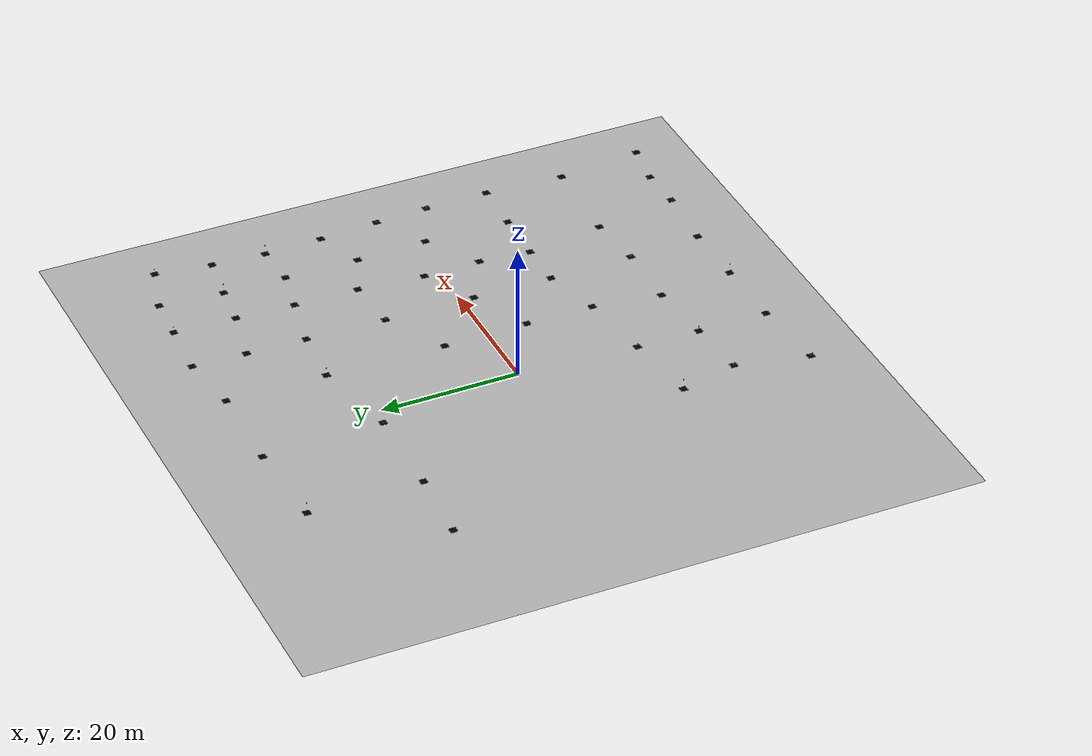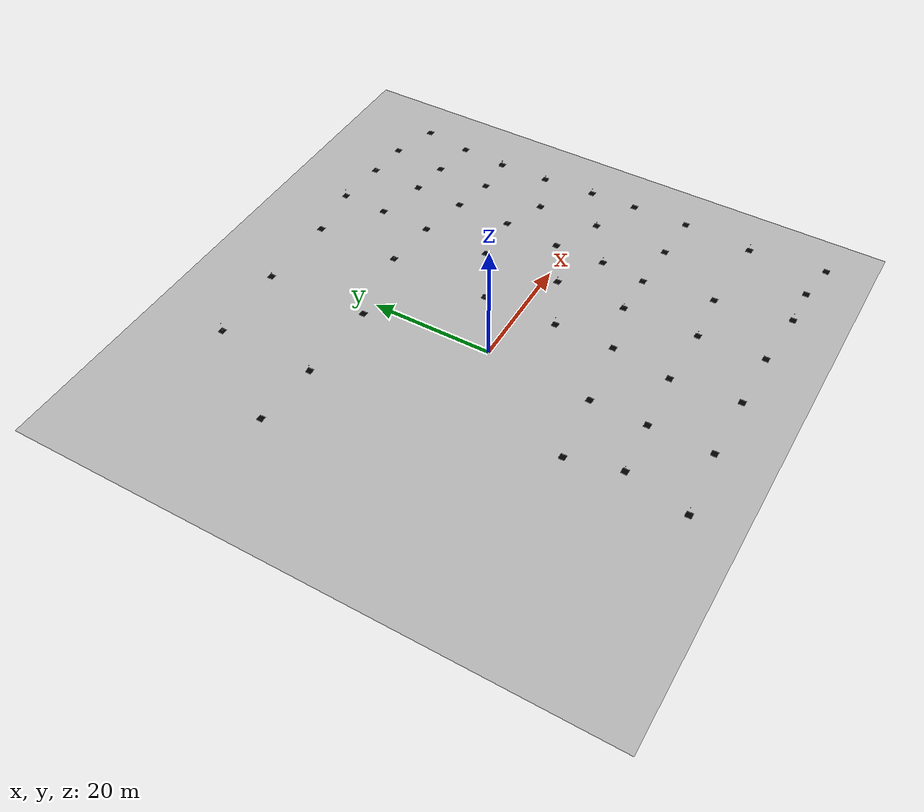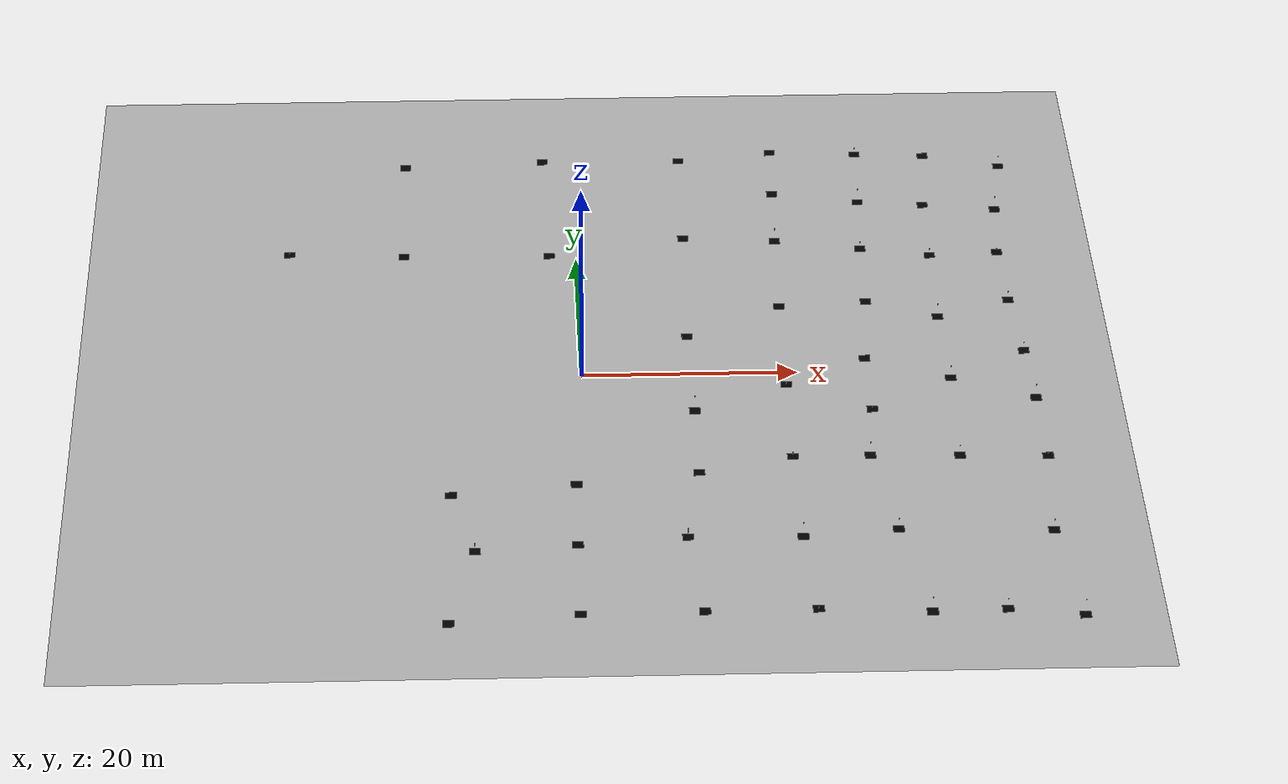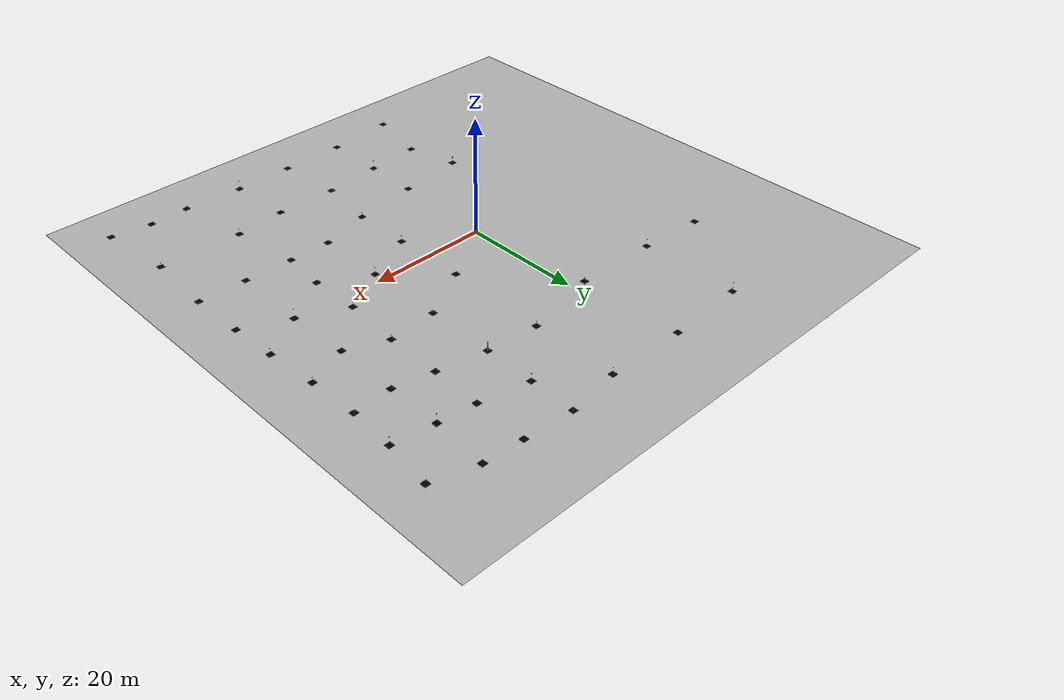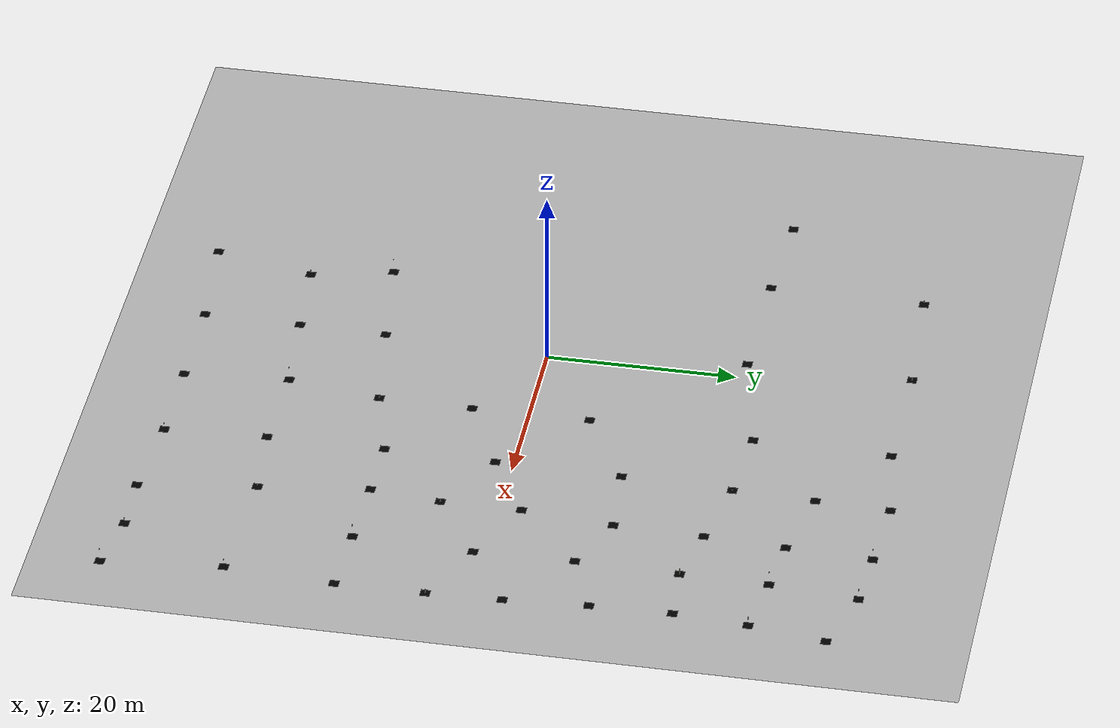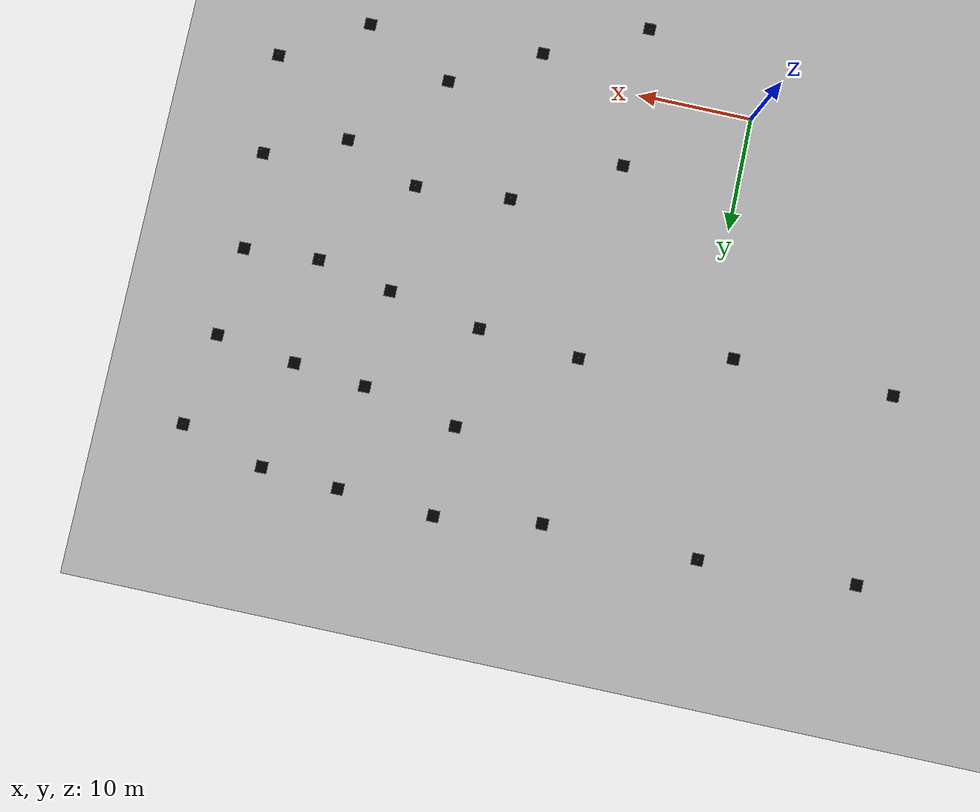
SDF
<sdf version="1.7">
 <world name="default">
  <light name="sun" type="directional">
   <pose>0 0 10 0 -0 0</pose>
   <diffuse>0.8 0.8 0.8 1</diffuse>
   <specular>0.2 0.2 0.2 1</specular>
   <attenuation>
    <range>1000</range>
    <constant>0.9</constant>
    <linear>0.01</linear>
    <quadratic>0.001</quadratic>
   </attenuation>
   <direction>-0.5 0.1 -0.9</direction>
   <spot><inner_angle>0</inner_angle><outer_angle>0</outer_angle><falloff>0</falloff></spot>
  </light>
  <gravity>0 0 -9.8</gravity>
  <magnetic_field>6e-06 2.3e-05 -4.2e-05</magnetic_field>
  <atmosphere type="adiabatic"/>
  <physics type="ode">
   <max_step_size>0.001</max_step_size>
   <real_time_factor>1</real_time_factor>
   <real_time_update_rate>1000</real_time_update_rate>
  </physics>
  <scene><ambient>0.4 0.4 0.4 1</ambient><background>0.7 0.7 0.7 1</background><shadows>1</shadows></scene>
  <spherical_coordinates>
   <surface_model>EARTH_WGS84</surface_model>
   <latitude_deg>0</latitude_deg>
   <longitude_deg>0</longitude_deg>
   <elevation>0</elevation>
   <heading_deg>0</heading_deg>
  </spherical_coordinates>
  <model name="grass">
   <pose>1.44006 2.40824 -0.01 0 -0 0</pose>
   <static>1</static>
   <link name="body">
    <visual name="visual">
     <geometry><mesh><uri>model://grass/media/grass.dae</uri></mesh></geometry>
     <material><script><uri>model://grass/media/Textures/</uri><name>__default__</name></script></material>
    </visual>
    <collision name="collision">
     <geometry><mesh><uri>model://grass/media/grass.dae</uri></mesh></geometry>
    </collision>
   </link>
  </model>
  <model name="macz">
   <static>1</static>
   <link name="pad">
    <collision name="collision"><geometry><box><size>1 1 0.001</size></box></geometry></collision>
    <visual name="visual">
     <cast_shadows>0</cast_shadows>
     <geometry><box><size>1 1 0.001</size></box></geometry>
     <material>
      <script>
       <uri>model://macz/materials/scripts</uri>
       <uri>model://macz/materials/textures</uri>
       <name>macz/ci</name>
      </script>
      <diffuse>0 0 0 1</diffuse>
     </material>
    </visual>
   </link>
   <link name="tube">
    <collision name="collision">
     <pose>0 0 0.8 0 -0 0</pose>
     <geometry>
      <mesh><uri>model://tube_9_5mm/meshes/tube_9_5.dae</uri><scale>0.6 0.6 10.526</scale></mesh>
     </geometry>
    </collision>
    <visual name="visual">
     <pose>0 0 0.8 0 -0 0</pose>
     <geometry>
      <mesh><uri>model://tube_9_5mm/meshes/tube_9_5.dae</uri><scale>0.6 0.6 10.526</scale></mesh>
     </geometry>
    </visual>
   </link>
   <pose>42.4382 -38.218 0 0 -0 0</pose>
  </model>
  <model name="macz_1">
   <static>1</static>
   <link name="pad">
    <collision name="collision"><geometry><box><size>1 1 0.001</size></box></geometry></collision>
    <visual name="visual">
     <cast_shadows>0</cast_shadows>
     <geometry><box><size>1 1 0.001</size></box></geometry>
     <material>
      <script>
       <uri>model://macz/materials/scripts</uri>
       <uri>model://macz/materials/textures</uri>
       <name>macz/ci</name>
      </script>
      <diffuse>0 0 0 1</diffuse>
     </material>
    </visual>
   </link>
   <link name="tube">
    <collision name="collision">
     <pose>0 0 0.8 0 -0 0</pose>
     <geometry>
      <mesh><uri>model://tube_9_5mm/meshes/tube_9_5.dae</uri><scale>0.6 0.6 10.526</scale></mesh>
     </geometry>
    </collision>
    <visual name="visual">
     <pose>0 0 0.8 0 -0 0</pose>
     <geometry>
      <mesh><uri>model://tube_9_5mm/meshes/tube_9_5.dae</uri><scale>0.6 0.6 10.526</scale></mesh>
     </geometry>
    </visual>
   </link>
   <pose>27.4285 21.2464 0 0 -0 0</pose>
  </model>
  <model name="macz_2">
   <static>1</static>
   <link name="pad">
    <collision name="collision"><geometry><box><size>1 1 0.001</size></box></geometry></collision>
    <visual name="visual">
     <cast_shadows>0</cast_shadows>
     <geometry><box><size>1 1 0.001</size></box></geometry>
     <material>
      <script>
       <uri>model://macz/materials/scripts</uri>
       <uri>model://macz/materials/textures</uri>
       <name>macz/ci</name>
      </script>
      <diffuse>0 0 0 1</diffuse>
     </material>
    </visual>
   </link>
   <link name="tube">
    <collision name="collision">
     <pose>0 0 0.8 0 -0 0</pose>
     <geometry>
      <mesh><uri>model://tube_9_5mm/meshes/tube_9_5.dae</uri><scale>0.6 0.6 10.526</scale></mesh>
     </geometry>
    </collision>
    <visual name="visual">
     <pose>0 0 0.8 0 -0 0</pose>
     <geometry>
      <mesh><uri>model://tube_9_5mm/meshes/tube_9_5.dae</uri><scale>0.6 0.6 10.526</scale></mesh>
     </geometry>
    </visual>
   </link>
   <pose>42.2532 36.1154 0 0 -0 0</pose>
  </model>
  <model name="parch">
   <static>1</static>
   <link name="pad">
    <collision name="collision"><geometry><box><size>1 1 0.001</size></box></geometry></collision>
    <visual name="visual">
     <cast_shadows>0</cast_shadows>
     <geometry><box><size>1 1 0.001</size></box></geometry>
     <material>
      <script>
       <uri>model://parch/materials/scripts</uri>
       <uri>model://parch/materials/textures</uri>
       <name>parch/circle</name>
      </script>
      <diffuse>0 0 0 1</diffuse>
     </material>
    </visual>
   </link>
   <link name="tube">
    <collision name="collision">
     <pose>0 0 0.8 0 -0 0</pose>
     <geometry>
      <mesh><uri>model://tube_9_5mm/meshes/tube_9_5.dae</uri><scale>0.6 0.6 10.526</scale></mesh>
     </geometry>
    </collision>
    <visual name="visual">
     <pose>0 0 0.8 0 -0 0</pose>
     <geometry>
      <mesh><uri>model://tube_9_5mm/meshes/tube_9_5.dae</uri><scale>0.6 0.6 10.526</scale></mesh>
     </geometry>
    </visual>
   </link>
   <pose>25.7384 -13.6505 0 0 -0 0</pose>
  </model>
  <model name="parch_0">
   <static>1</static>
   <link name="pad">
    <collision name="collision"><geometry><box><size>1 1 0.001</size></box></geometry></collision>
    <visual name="visual">
     <cast_shadows>0</cast_shadows>
     <geometry><box><size>1 1 0.001</size></box></geometry>
     <material>
      <script>
       <uri>model://parch/materials/scripts</uri>
       <uri>model://parch/materials/textures</uri>
       <name>parch/circle</name>
      </script>
      <diffuse>0 0 0 1</diffuse>
     </material>
    </visual>
   </link>
   <link name="tube">
    <collision name="collision">
     <pose>0 0 0.8 0 -0 0</pose>
     <geometry>
      <mesh><uri>model://tube_9_5mm/meshes/tube_9_5.dae</uri><scale>0.6 0.6 10.526</scale></mesh>
     </geometry>
    </collision>
    <visual name="visual">
     <pose>0 0 0.8 0 -0 0</pose>
     <geometry>
      <mesh><uri>model://tube_9_5mm/meshes/tube_9_5.dae</uri><scale>0.6 0.6 10.526</scale></mesh>
     </geometry>
    </visual>
   </link>
   <pose>41.8058 -14.1457 0 0 -0 0</pose>
  </model>
  <model name="parch_1">
   <static>1</static>
   <link name="pad">
    <collision name="collision"><geometry><box><size>1 1 0.001</size></box></geometry></collision>
    <visual name="visual">
     <cast_shadows>0</cast_shadows>
     <geometry><box><size>1 1 0.001</size></box></geometry>
     <material>
      <script>
       <uri>model://parch/materials/scripts</uri>
       <uri>model://parch/materials/textures</uri>
       <name>parch/circle</name>
      </script>
      <diffuse>0 0 0 1</diffuse>
     </material>
    </visual>
   </link>
   <link name="tube">
    <collision name="collision">
     <pose>0 0 0.8 0 -0 0</pose>
     <geometry>
      <mesh><uri>model://tube_9_5mm/meshes/tube_9_5.dae</uri><scale>0.6 0.6 10.526</scale></mesh>
     </geometry>
    </collision>
    <visual name="visual">
     <pose>0 0 0.8 0 -0 0</pose>
     <geometry>
      <mesh><uri>model://tube_9_5mm/meshes/tube_9_5.dae</uri><scale>0.6 0.6 10.526</scale></mesh>
     </geometry>
    </visual>
   </link>
   <pose>40.5371 20.2628 0 0 -0 0</pose>
  </model>
  <model name="healthy">
   <static>1</static>
   <link name="pad">
    <collision name="collision"><geometry><box><size>1 1 0.001</size></box></geometry></collision>
    <visual name="visual">
     <cast_shadows>0</cast_shadows>
     <geometry><box><size>1 1 0.001</size></box></geometry>
     <material>
      <script>
       <uri>model://healthy/materials/scripts</uri>
       <uri>model://healthy/materials/textures</uri>
       <name>healthy/ci</name>
      </script>
      <diffuse>0 0 0 1</diffuse>
     </material>
    </visual>
   </link>
   <link name="tube">
    <collision name="collision">
     <pose>0 0 0.8 0 -0 0</pose>
     <geometry>
      <mesh><uri>model://tube_9_5mm/meshes/tube_9_5.dae</uri><scale>0.6 0.6 10.526</scale></mesh>
     </geometry>
    </collision>
    <visual name="visual">
     <pose>0 0 0.8 0 -0 0</pose>
     <geometry>
      <mesh><uri>model://tube_9_5mm/meshes/tube_9_5.dae</uri><scale>0.6 0.6 10.526</scale></mesh>
     </geometry>
    </visual>
   </link>
   <pose>9.66173 -36.7666 0 0 -0 0</pose>
  </model>
  <model name="healthy_0">
   <static>1</static>
   <link name="pad">
    <collision name="collision"><geometry><box><size>1 1 0.001</size></box></geometry></collision>
    <visual name="visual">
     <cast_shadows>0</cast_shadows>
     <geometry><box><size>1 1 0.001</size></box></geometry>
     <material>
      <script>
       <uri>model://healthy/materials/scripts</uri>
       <uri>model://healthy/materials/textures</uri>
       <name>healthy/ci</name>
      </script>
      <diffuse>0 0 0 1</diffuse>
     </material>
    </visual>
   </link>
   <link name="tube">
    <collision name="collision">
     <pose>0 0 0.8 0 -0 0</pose>
     <geometry>
      <mesh><uri>model://tube_9_5mm/meshes/tube_9_5.dae</uri><scale>0.6 0.6 10.526</scale></mesh>
     </geometry>
    </collision>
    <visual name="visual">
     <pose>0 0 0.8 0 -0 0</pose>
     <geometry>
      <mesh><uri>model://tube_9_5mm/meshes/tube_9_5.dae</uri><scale>0.6 0.6 10.526</scale></mesh>
     </geometry>
    </visual>
   </link>
   <pose>29.3036 -37.3707 0 0 -0 0</pose>
  </model>
  <model name="healthy_1">
   <static>1</static>
   <link name="pad">
    <collision name="collision"><geometry><box><size>1 1 0.001</size></box></geometry></collision>
    <visual name="visual">
     <cast_shadows>0</cast_shadows>
     <geometry><box><size>1 1 0.001</size></box></geometry>
     <material>
      <script>
       <uri>model://healthy/materials/scripts</uri>
       <uri>model://healthy/materials/textures</uri>
       <name>healthy/ci</name>
      </script>
      <diffuse>0 0 0 1</diffuse>
     </material>
    </visual>
   </link>
   <link name="tube">
    <collision name="collision">
     <pose>0 0 0.8 0 -0 0</pose>
     <geometry>
      <mesh><uri>model://tube_9_5mm/meshes/tube_9_5.dae</uri><scale>0.6 0.6 10.526</scale></mesh>
     </geometry>
    </collision>
    <visual name="visual">
     <pose>0 0 0.8 0 -0 0</pose>
     <geometry>
      <mesh><uri>model://tube_9_5mm/meshes/tube_9_5.dae</uri><scale>0.6 0.6 10.526</scale></mesh>
     </geometry>
    </visual>
   </link>
   <pose>28.1736 38.7167 0 0 -0 0</pose>
  </model>
  <model name="healthy_2">
   <static>1</static>
   <link name="pad">
    <collision name="collision"><geometry><box><size>1 1 0.001</size></box></geometry></collision>
    <visual name="visual">
     <cast_shadows>0</cast_shadows>
     <geometry><box><size>1 1 0.001</size></box></geometry>
     <material>
      <script>
       <uri>model://healthy/materials/scripts</uri>
       <uri>model://healthy/materials/textures</uri>
       <name>healthy/ci</name>
      </script>
      <diffuse>0 0 0 1</diffuse>
     </material>
    </visual>
   </link>
   <link name="tube">
    <collision name="collision">
     <pose>0 0 0.8 0 -0 0</pose>
     <geometry>
      <mesh><uri>model://tube_9_5mm/meshes/tube_9_5.dae</uri><scale>0.6 0.6 10.526</scale></mesh>
     </geometry>
    </collision>
    <visual name="visual">
     <pose>0 0 0.8 0 -0 0</pose>
     <geometry>
      <mesh><uri>model://tube_9_5mm/meshes/tube_9_5.dae</uri><scale>0.6 0.6 10.526</scale></mesh>
     </geometry>
    </visual>
   </link>
   <pose>-12.4812 -37.9052 0 0 -0 0</pose>
  </model>
  <model name="healthy_3">
   <static>1</static>
   <link name="pad">
    <collision name="collision"><geometry><box><size>1 1 0.001</size></box></geometry></collision>
    <visual name="visual">
     <cast_shadows>0</cast_shadows>
     <geometry><box><size>1 1 0.001</size></box></geometry>
     <material>
      <script>
       <uri>model://healthy/materials/scripts</uri>
       <uri>model://healthy/materials/textures</uri>
       <name>healthy/ci</name>
      </script>
      <diffuse>0 0 0 1</diffuse>
     </material>
    </visual>
   </link>
   <link name="tube">
    <collision name="collision">
     <pose>0 0 0.8 0 -0 0</pose>
     <geometry>
      <mesh><uri>model://tube_9_5mm/meshes/tube_9_5.dae</uri><scale>0.6 0.6 10.526</scale></mesh>
     </geometry>
    </collision>
    <visual name="visual">
     <pose>0 0 0.8 0 -0 0</pose>
     <geometry>
      <mesh><uri>model://tube_9_5mm/meshes/tube_9_5.dae</uri><scale>0.6 0.6 10.526</scale></mesh>
     </geometry>
    </visual>
   </link>
   <pose>-12.185 -18.8259 0 0 -0 0</pose>
  </model>
  <model name="healthy_4">
   <static>1</static>
   <link name="pad">
    <collision name="collision"><geometry><box><size>1 1 0.001</size></box></geometry></collision>
    <visual name="visual">
     <cast_shadows>0</cast_shadows>
     <geometry><box><size>1 1 0.001</size></box></geometry>
     <material>
      <script>
       <uri>model://healthy/materials/scripts</uri>
       <uri>model://healthy/materials/textures</uri>
       <name>healthy/ci</name>
      </script>
      <diffuse>0 0 0 1</diffuse>
     </material>
    </visual>
   </link>
   <link name="tube">
    <collision name="collision">
     <pose>0 0 0.8 0 -0 0</pose>
     <geometry>
      <mesh><uri>model://tube_9_5mm/meshes/tube_9_5.dae</uri><scale>0.6 0.6 10.526</scale></mesh>
     </geometry>
    </collision>
    <visual name="visual">
     <pose>0 0 0.8 0 -0 0</pose>
     <geometry>
      <mesh><uri>model://tube_9_5mm/meshes/tube_9_5.dae</uri><scale>0.6 0.6 10.526</scale></mesh>
     </geometry>
    </visual>
   </link>
   <pose>10.1604 -15.8832 0 0 -0 0</pose>
  </model>
  <model name="healthy_5">
   <static>1</static>
   <link name="pad">
    <collision name="collision"><geometry><box><size>1 1 0.001</size></box></geometry></collision>
    <visual name="visual">
     <cast_shadows>0</cast_shadows>
     <geometry><box><size>1 1 0.001</size></box></geometry>
     <material>
      <script>
       <uri>model://healthy/materials/scripts</uri>
       <uri>model://healthy/materials/textures</uri>
       <name>healthy/ci</name>
      </script>
      <diffuse>0 0 0 1</diffuse>
     </material>
    </visual>
   </link>
   <link name="tube">
    <collision name="collision">
     <pose>0 0 0.8 0 -0 0</pose>
     <geometry>
      <mesh><uri>model://tube_9_5mm/meshes/tube_9_5.dae</uri><scale>0.6 0.6 10.526</scale></mesh>
     </geometry>
    </collision>
    <visual name="visual">
     <pose>0 0 0.8 0 -0 0</pose>
     <geometry>
      <mesh><uri>model://tube_9_5mm/meshes/tube_9_5.dae</uri><scale>0.6 0.6 10.526</scale></mesh>
     </geometry>
    </visual>
   </link>
   <pose>10.0566 6.33012 0 0 -0 0</pose>
  </model>
  <model name="healthy_6">
   <static>1</static>
   <link name="pad">
    <collision name="collision"><geometry><box><size>1 1 0.001</size></box></geometry></collision>
    <visual name="visual">
     <cast_shadows>0</cast_shadows>
     <geometry><box><size>1 1 0.001</size></box></geometry>
     <material>
      <script>
       <uri>model://healthy/materials/scripts</uri>
       <uri>model://healthy/materials/textures</uri>
       <name>healthy/ci</name>
      </script>
      <diffuse>0 0 0 1</diffuse>
     </material>
    </visual>
   </link>
   <link name="tube">
    <collision name="collision">
     <pose>0 0 0.8 0 -0 0</pose>
     <geometry>
      <mesh><uri>model://tube_9_5mm/meshes/tube_9_5.dae</uri><scale>0.6 0.6 10.526</scale></mesh>
     </geometry>
    </collision>
    <visual name="visual">
     <pose>0 0 0.8 0 -0 0</pose>
     <geometry>
      <mesh><uri>model://tube_9_5mm/meshes/tube_9_5.dae</uri><scale>0.6 0.6 10.526</scale></mesh>
     </geometry>
    </visual>
   </link>
   <pose>10.4363 23.5417 0 0 -0 0</pose>
  </model>
  <model name="healthy_7">
   <static>1</static>
   <link name="pad">
    <collision name="collision"><geometry><box><size>1 1 0.001</size></box></geometry></collision>
    <visual name="visual">
     <cast_shadows>0</cast_shadows>
     <geometry><box><size>1 1 0.001</size></box></geometry>
     <material>
      <script>
       <uri>model://healthy/materials/scripts</uri>
       <uri>model://healthy/materials/textures</uri>
       <name>healthy/ci</name>
      </script>
      <diffuse>0 0 0 1</diffuse>
     </material>
    </visual>
   </link>
   <link name="tube">
    <collision name="collision">
     <pose>0 0 0.8 0 -0 0</pose>
     <geometry>
      <mesh><uri>model://tube_9_5mm/meshes/tube_9_5.dae</uri><scale>0.6 0.6 10.526</scale></mesh>
     </geometry>
    </collision>
    <visual name="visual">
     <pose>0 0 0.8 0 -0 0</pose>
     <geometry>
      <mesh><uri>model://tube_9_5mm/meshes/tube_9_5.dae</uri><scale>0.6 0.6 10.526</scale></mesh>
     </geometry>
    </visual>
   </link>
   <pose>10.589 37.9867 0 0 -0 0</pose>
  </model>
  <model name="healthy_8">
   <static>1</static>
   <link name="pad">
    <collision name="collision"><geometry><box><size>1 1 0.001</size></box></geometry></collision>
    <visual name="visual">
     <cast_shadows>0</cast_shadows>
     <geometry><box><size>1 1 0.001</size></box></geometry>
     <material>
      <script>
       <uri>model://healthy/materials/scripts</uri>
       <uri>model://healthy/materials/textures</uri>
       <name>healthy/ci</name>
      </script>
      <diffuse>0 0 0 1</diffuse>
     </material>
    </visual>
   </link>
   <link name="tube">
    <collision name="collision">
     <pose>0 0 0.8 0 -0 0</pose>
     <geometry>
      <mesh><uri>model://tube_9_5mm/meshes/tube_9_5.dae</uri><scale>0.6 0.6 10.526</scale></mesh>
     </geometry>
    </collision>
    <visual name="visual">
     <pose>0 0 0.8 0 -0 0</pose>
     <geometry>
      <mesh><uri>model://tube_9_5mm/meshes/tube_9_5.dae</uri><scale>0.6 0.6 10.526</scale></mesh>
     </geometry>
    </visual>
   </link>
   <pose>-2.86503 38.1746 0 0 -0 0</pose>
  </model>
  <model name="healthy_9">
   <static>1</static>
   <link name="pad">
    <collision name="collision"><geometry><box><size>1 1 0.001</size></box></geometry></collision>
    <visual name="visual">
     <cast_shadows>0</cast_shadows>
     <geometry><box><size>1 1 0.001</size></box></geometry>
     <material>
      <script>
       <uri>model://healthy/materials/scripts</uri>
       <uri>model://healthy/materials/textures</uri>
       <name>healthy/ci</name>
      </script>
      <diffuse>0 0 0 1</diffuse>
     </material>
    </visual>
   </link>
   <link name="tube">
    <collision name="collision">
     <pose>0 0 0.8 0 -0 0</pose>
     <geometry>
      <mesh><uri>model://tube_9_5mm/meshes/tube_9_5.dae</uri><scale>0.6 0.6 10.526</scale></mesh>
     </geometry>
    </collision>
    <visual name="visual">
     <pose>0 0 0.8 0 -0 0</pose>
     <geometry>
      <mesh><uri>model://tube_9_5mm/meshes/tube_9_5.dae</uri><scale>0.6 0.6 10.526</scale></mesh>
     </geometry>
    </visual>
   </link>
   <pose>-2.54751 20.823 0 0 -0 0</pose>
  </model>
  <model name="healthy_10">
   <static>1</static>
   <link name="pad">
    <collision name="collision"><geometry><box><size>1 1 0.001</size></box></geometry></collision>
    <visual name="visual">
     <cast_shadows>0</cast_shadows>
     <geometry><box><size>1 1 0.001</size></box></geometry>
     <material>
      <script>
       <uri>model://healthy/materials/scripts</uri>
       <uri>model://healthy/materials/textures</uri>
       <name>healthy/ci</name>
      </script>
      <diffuse>0 0 0 1</diffuse>
     </material>
    </visual>
   </link>
   <link name="tube">
    <collision name="collision">
     <pose>0 0 0.8 0 -0 0</pose>
     <geometry>
      <mesh><uri>model://tube_9_5mm/meshes/tube_9_5.dae</uri><scale>0.6 0.6 10.526</scale></mesh>
     </geometry>
    </collision>
    <visual name="visual">
     <pose>0 0 0.8 0 -0 0</pose>
     <geometry>
      <mesh><uri>model://tube_9_5mm/meshes/tube_9_5.dae</uri><scale>0.6 0.6 10.526</scale></mesh>
     </geometry>
    </visual>
   </link>
   <pose>-16.4981 21.0733 0 0 -0 0</pose>
  </model>
  <model name="healthy_11">
   <static>1</static>
   <link name="pad">
    <collision name="collision"><geometry><box><size>1 1 0.001</size></box></geometry></collision>
    <visual name="visual">
     <cast_shadows>0</cast_shadows>
     <geometry><box><size>1 1 0.001</size></box></geometry>
     <material>
      <script>
       <uri>model://healthy/materials/scripts</uri>
       <uri>model://healthy/materials/textures</uri>
       <name>healthy/ci</name>
      </script>
      <diffuse>0 0 0 1</diffuse>
     </material>
    </visual>
   </link>
   <link name="tube">
    <collision name="collision">
     <pose>0 0 0.8 0 -0 0</pose>
     <geometry>
      <mesh><uri>model://tube_9_5mm/meshes/tube_9_5.dae</uri><scale>0.6 0.6 10.526</scale></mesh>
     </geometry>
    </collision>
    <visual name="visual">
     <pose>0 0 0.8 0 -0 0</pose>
     <geometry>
      <mesh><uri>model://tube_9_5mm/meshes/tube_9_5.dae</uri><scale>0.6 0.6 10.526</scale></mesh>
     </geometry>
    </visual>
   </link>
   <pose>-16.4011 37.4587 0 0 -0 0</pose>
  </model>
  <model name="healthy_12">
   <static>1</static>
   <link name="pad">
    <collision name="collision"><geometry><box><size>1 1 0.001</size></box></geometry></collision>
    <visual name="visual">
     <cast_shadows>0</cast_shadows>
     <geometry><box><size>1 1 0.001</size></box></geometry>
     <material>
      <script>
       <uri>model://healthy/materials/scripts</uri>
       <uri>model://healthy/materials/textures</uri>
       <name>healthy/ci</name>
      </script>
      <diffuse>0 0 0 1</diffuse>
     </material>
    </visual>
   </link>
   <link name="tube">
    <collision name="collision">
     <pose>0 0 0.8 0 -0 0</pose>
     <geometry>
      <mesh><uri>model://tube_9_5mm/meshes/tube_9_5.dae</uri><scale>0.6 0.6 10.526</scale></mesh>
     </geometry>
    </collision>
    <visual name="visual">
     <pose>0 0 0.8 0 -0 0</pose>
     <geometry>
      <mesh><uri>model://tube_9_5mm/meshes/tube_9_5.dae</uri><scale>0.6 0.6 10.526</scale></mesh>
     </geometry>
    </visual>
   </link>
   <pose>-27.5068 21.7252 0 0 -0 0</pose>
  </model>
  <model name="healthy_13">
   <static>1</static>
   <link name="pad">
    <collision name="collision"><geometry><box><size>1 1 0.001</size></box></geometry></collision>
    <visual name="visual">
     <cast_shadows>0</cast_shadows>
     <geometry><box><size>1 1 0.001</size></box></geometry>
     <material>
      <script>
       <uri>model://healthy/materials/scripts</uri>
       <uri>model://healthy/materials/textures</uri>
       <name>healthy/ci</name>
      </script>
      <diffuse>0 0 0 1</diffuse>
     </material>
    </visual>
   </link>
   <link name="tube">
    <collision name="collision">
     <pose>0 0 0.8 0 -0 0</pose>
     <geometry>
      <mesh><uri>model://tube_9_5mm/meshes/tube_9_5.dae</uri><scale>0.6 0.6 10.526</scale></mesh>
     </geometry>
    </collision>
    <visual name="visual">
     <pose>0 0 0.8 0 -0 0</pose>
     <geometry>
      <mesh><uri>model://tube_9_5mm/meshes/tube_9_5.dae</uri><scale>0.6 0.6 10.526</scale></mesh>
     </geometry>
    </visual>
   </link>
   <pose>33.8331 -13.8875 0 0 -0 0</pose>
  </model>
  <model name="healthy_14">
   <static>1</static>
   <link name="pad">
    <collision name="collision"><geometry><box><size>1 1 0.001</size></box></geometry></collision>
    <visual name="visual">
     <cast_shadows>0</cast_shadows>
     <geometry><box><size>1 1 0.001</size></box></geometry>
     <material>
      <script>
       <uri>model://healthy/materials/scripts</uri>
       <uri>model://healthy/materials/textures</uri>
       <name>healthy/ci</name>
      </script>
      <diffuse>0 0 0 1</diffuse>
     </material>
    </visual>
   </link>
   <link name="tube">
    <collision name="collision">
     <pose>0 0 0.8 0 -0 0</pose>
     <geometry>
      <mesh><uri>model://tube_9_5mm/meshes/tube_9_5.dae</uri><scale>0.6 0.6 10.526</scale></mesh>
     </geometry>
    </collision>
    <visual name="visual">
     <pose>0 0 0.8 0 -0 0</pose>
     <geometry>
      <mesh><uri>model://tube_9_5mm/meshes/tube_9_5.dae</uri><scale>0.6 0.6 10.526</scale></mesh>
     </geometry>
    </visual>
   </link>
   <pose>27.3685 -25.1445 0 0 -0 0</pose>
  </model>
  <model name="healthy_15">
   <static>1</static>
   <link name="pad">
    <collision name="collision"><geometry><box><size>1 1 0.001</size></box></geometry></collision>
    <visual name="visual">
     <cast_shadows>0</cast_shadows>
     <geometry><box><size>1 1 0.001</size></box></geometry>
     <material>
      <script>
       <uri>model://healthy/materials/scripts</uri>
       <uri>model://healthy/materials/textures</uri>
       <name>healthy/ci</name>
      </script>
      <diffuse>0 0 0 1</diffuse>
     </material>
    </visual>
   </link>
   <link name="tube">
    <collision name="collision">
     <pose>0 0 0.8 0 -0 0</pose>
     <geometry>
      <mesh><uri>model://tube_9_5mm/meshes/tube_9_5.dae</uri><scale>0.6 0.6 10.526</scale></mesh>
     </geometry>
    </collision>
    <visual name="visual">
     <pose>0 0 0.8 0 -0 0</pose>
     <geometry>
      <mesh><uri>model://tube_9_5mm/meshes/tube_9_5.dae</uri><scale>0.6 0.6 10.526</scale></mesh>
     </geometry>
    </visual>
   </link>
   <pose>41.3759 3.04051 0 0 -0 0</pose>
  </model>
  <model name="healthy_16">
   <static>1</static>
   <link name="pad">
    <collision name="collision"><geometry><box><size>1 1 0.001</size></box></geometry></collision>
    <visual name="visual">
     <cast_shadows>0</cast_shadows>
     <geometry><box><size>1 1 0.001</size></box></geometry>
     <material>
      <script>
       <uri>model://healthy/materials/scripts</uri>
       <uri>model://healthy/materials/textures</uri>
       <name>healthy/ci</name>
      </script>
      <diffuse>0 0 0 1</diffuse>
     </material>
    </visual>
   </link>
   <link name="tube">
    <collision name="collision">
     <pose>0 0 0.8 0 -0 0</pose>
     <geometry>
      <mesh><uri>model://tube_9_5mm/meshes/tube_9_5.dae</uri><scale>0.6 0.6 10.526</scale></mesh>
     </geometry>
    </collision>
    <visual name="visual">
     <pose>0 0 0.8 0 -0 0</pose>
     <geometry>
      <mesh><uri>model://tube_9_5mm/meshes/tube_9_5.dae</uri><scale>0.6 0.6 10.526</scale></mesh>
     </geometry>
    </visual>
   </link>
   <pose>26.4073 2.20253 0 0 -0 0</pose>
  </model>
  <model name="healthy_17">
   <static>1</static>
   <link name="pad">
    <collision name="collision"><geometry><box><size>1 1 0.001</size></box></geometry></collision>
    <visual name="visual">
     <cast_shadows>0</cast_shadows>
     <geometry><box><size>1 1 0.001</size></box></geometry>
     <material>
      <script>
       <uri>model://healthy/materials/scripts</uri>
       <uri>model://healthy/materials/textures</uri>
       <name>healthy/ci</name>
      </script>
      <diffuse>0 0 0 1</diffuse>
     </material>
    </visual>
   </link>
   <link name="tube">
    <collision name="collision">
     <pose>0 0 0.8 0 -0 0</pose>
     <geometry>
      <mesh><uri>model://tube_9_5mm/meshes/tube_9_5.dae</uri><scale>0.6 0.6 10.526</scale></mesh>
     </geometry>
    </collision>
    <visual name="visual">
     <pose>0 0 0.8 0 -0 0</pose>
     <geometry>
      <mesh><uri>model://tube_9_5mm/meshes/tube_9_5.dae</uri><scale>0.6 0.6 10.526</scale></mesh>
     </geometry>
    </visual>
   </link>
   <pose>41.1023 28.0364 0 0 -0 0</pose>
  </model>
  <model name="healthy_18">
   <static>1</static>
   <link name="pad">
    <collision name="collision"><geometry><box><size>1 1 0.001</size></box></geometry></collision>
    <visual name="visual">
     <cast_shadows>0</cast_shadows>
     <geometry><box><size>1 1 0.001</size></box></geometry>
     <material>
      <script>
       <uri>model://healthy/materials/scripts</uri>
       <uri>model://healthy/materials/textures</uri>
       <name>healthy/ci</name>
      </script>
      <diffuse>0 0 0 1</diffuse>
     </material>
    </visual>
   </link>
   <link name="tube">
    <collision name="collision">
     <pose>0 0 0.8 0 -0 0</pose>
     <geometry>
      <mesh><uri>model://tube_9_5mm/meshes/tube_9_5.dae</uri><scale>0.6 0.6 10.526</scale></mesh>
     </geometry>
    </collision>
    <visual name="visual">
     <pose>0 0 0.8 0 -0 0</pose>
     <geometry>
      <mesh><uri>model://tube_9_5mm/meshes/tube_9_5.dae</uri><scale>0.6 0.6 10.526</scale></mesh>
     </geometry>
    </visual>
   </link>
   <pose>40.7801 11.7874 0 0 -0 0</pose>
  </model>
  <model name="healthy_19">
   <static>1</static>
   <link name="pad">
    <collision name="collision"><geometry><box><size>1 1 0.001</size></box></geometry></collision>
    <visual name="visual">
     <cast_shadows>0</cast_shadows>
     <geometry><box><size>1 1 0.001</size></box></geometry>
     <material>
      <script>
       <uri>model://healthy/materials/scripts</uri>
       <uri>model://healthy/materials/textures</uri>
       <name>healthy/ci</name>
      </script>
      <diffuse>0 0 0 1</diffuse>
     </material>
    </visual>
   </link>
   <link name="tube">
    <collision name="collision">
     <pose>0 0 0.8 0 -0 0</pose>
     <geometry>
      <mesh><uri>model://tube_9_5mm/meshes/tube_9_5.dae</uri><scale>0.6 0.6 10.526</scale></mesh>
     </geometry>
    </collision>
    <visual name="visual">
     <pose>0 0 0.8 0 -0 0</pose>
     <geometry>
      <mesh><uri>model://tube_9_5mm/meshes/tube_9_5.dae</uri><scale>0.6 0.6 10.526</scale></mesh>
     </geometry>
    </visual>
   </link>
   <pose>41.0979 -25.6819 0 0 -0 0</pose>
  </model>
  <model name="healthy_20">
   <static>1</static>
   <link name="pad">
    <collision name="collision"><geometry><box><size>1 1 0.001</size></box></geometry></collision>
    <visual name="visual">
     <cast_shadows>0</cast_shadows>
     <geometry><box><size>1 1 0.001</size></box></geometry>
     <material>
      <script>
       <uri>model://healthy/materials/scripts</uri>
       <uri>model://healthy/materials/textures</uri>
       <name>healthy/ci</name>
      </script>
      <diffuse>0 0 0 1</diffuse>
     </material>
    </visual>
   </link>
   <link name="tube">
    <collision name="collision">
     <pose>0 0 0.8 0 -0 0</pose>
     <geometry>
      <mesh><uri>model://tube_9_5mm/meshes/tube_9_5.dae</uri><scale>0.6 0.6 10.526</scale></mesh>
     </geometry>
    </collision>
    <visual name="visual">
     <pose>0 0 0.8 0 -0 0</pose>
     <geometry>
      <mesh><uri>model://tube_9_5mm/meshes/tube_9_5.dae</uri><scale>0.6 0.6 10.526</scale></mesh>
     </geometry>
    </visual>
   </link>
   <pose>-1.10612 -36.89 0 0 -0 0</pose>
  </model>
  <model name="healthy_21">
   <static>1</static>
   <link name="pad">
    <collision name="collision"><geometry><box><size>1 1 0.001</size></box></geometry></collision>
    <visual name="visual">
     <cast_shadows>0</cast_shadows>
     <geometry><box><size>1 1 0.001</size></box></geometry>
     <material>
      <script>
       <uri>model://healthy/materials/scripts</uri>
       <uri>model://healthy/materials/textures</uri>
       <name>healthy/ci</name>
      </script>
      <diffuse>0 0 0 1</diffuse>
     </material>
    </visual>
   </link>
   <link name="tube">
    <collision name="collision">
     <pose>0 0 0.8 0 -0 0</pose>
     <geometry>
      <mesh><uri>model://tube_9_5mm/meshes/tube_9_5.dae</uri><scale>0.6 0.6 10.526</scale></mesh>
     </geometry>
    </collision>
    <visual name="visual">
     <pose>0 0 0.8 0 -0 0</pose>
     <geometry>
      <mesh><uri>model://tube_9_5mm/meshes/tube_9_5.dae</uri><scale>0.6 0.6 10.526</scale></mesh>
     </geometry>
    </visual>
   </link>
   <pose>-0.930026 -17.429 0 0 -0 0</pose>
  </model>
  <model name="healthy_22">
   <static>1</static>
   <link name="pad">
    <collision name="collision"><geometry><box><size>1 1 0.001</size></box></geometry></collision>
    <visual name="visual">
     <cast_shadows>0</cast_shadows>
     <geometry><box><size>1 1 0.001</size></box></geometry>
     <material>
      <script>
       <uri>model://healthy/materials/scripts</uri>
       <uri>model://healthy/materials/textures</uri>
       <name>healthy/ci</name>
      </script>
      <diffuse>0 0 0 1</diffuse>
     </material>
    </visual>
   </link>
   <link name="tube">
    <collision name="collision">
     <pose>0 0 0.8 0 -0 0</pose>
     <geometry>
      <mesh><uri>model://tube_9_5mm/meshes/tube_9_5.dae</uri><scale>0.6 0.6 10.526</scale></mesh>
     </geometry>
    </collision>
    <visual name="visual">
     <pose>0 0 0.8 0 -0 0</pose>
     <geometry>
      <mesh><uri>model://tube_9_5mm/meshes/tube_9_5.dae</uri><scale>0.6 0.6 10.526</scale></mesh>
     </geometry>
    </visual>
   </link>
   <pose>19.4897 -36.6904 0 0 -0 0</pose>
  </model>
  <model name="healthy_23">
   <static>1</static>
   <link name="pad">
    <collision name="collision"><geometry><box><size>1 1 0.001</size></box></geometry></collision>
    <visual name="visual">
     <cast_shadows>0</cast_shadows>
     <geometry><box><size>1 1 0.001</size></box></geometry>
     <material>
      <script>
       <uri>model://healthy/materials/scripts</uri>
       <uri>model://healthy/materials/textures</uri>
       <name>healthy/ci</name>
      </script>
      <diffuse>0 0 0 1</diffuse>
     </material>
    </visual>
   </link>
   <link name="tube">
    <collision name="collision">
     <pose>0 0 0.8 0 -0 0</pose>
     <geometry>
      <mesh><uri>model://tube_9_5mm/meshes/tube_9_5.dae</uri><scale>0.6 0.6 10.526</scale></mesh>
     </geometry>
    </collision>
    <visual name="visual">
     <pose>0 0 0.8 0 -0 0</pose>
     <geometry>
      <mesh><uri>model://tube_9_5mm/meshes/tube_9_5.dae</uri><scale>0.6 0.6 10.526</scale></mesh>
     </geometry>
    </visual>
   </link>
   <pose>26.5051 -6.22467 0 0 -0 0</pose>
  </model>
  <model name="healthy_24">
   <static>1</static>
   <link name="pad">
    <collision name="collision"><geometry><box><size>1 1 0.001</size></box></geometry></collision>
    <visual name="visual">
     <cast_shadows>0</cast_shadows>
     <geometry><box><size>1 1 0.001</size></box></geometry>
     <material>
      <script>
       <uri>model://healthy/materials/scripts</uri>
       <uri>model://healthy/materials/textures</uri>
       <name>healthy/ci</name>
      </script>
      <diffuse>0 0 0 1</diffuse>
     </material>
    </visual>
   </link>
   <link name="tube">
    <collision name="collision">
     <pose>0 0 0.8 0 -0 0</pose>
     <geometry>
      <mesh><uri>model://tube_9_5mm/meshes/tube_9_5.dae</uri><scale>0.6 0.6 10.526</scale></mesh>
     </geometry>
    </collision>
    <visual name="visual">
     <pose>0 0 0.8 0 -0 0</pose>
     <geometry>
      <mesh><uri>model://tube_9_5mm/meshes/tube_9_5.dae</uri><scale>0.6 0.6 10.526</scale></mesh>
     </geometry>
    </visual>
   </link>
   <pose>27.2387 11.8563 0 0 -0 0</pose>
  </model>
  <model name="healthy_25">
   <static>1</static>
   <link name="pad">
    <collision name="collision"><geometry><box><size>1 1 0.001</size></box></geometry></collision>
    <visual name="visual">
     <cast_shadows>0</cast_shadows>
     <geometry><box><size>1 1 0.001</size></box></geometry>
     <material>
      <script>
       <uri>model://healthy/materials/scripts</uri>
       <uri>model://healthy/materials/textures</uri>
       <name>healthy/ci</name>
      </script>
      <diffuse>0 0 0 1</diffuse>
     </material>
    </visual>
   </link>
   <link name="tube">
    <collision name="collision">
     <pose>0 0 0.8 0 -0 0</pose>
     <geometry>
      <mesh><uri>model://tube_9_5mm/meshes/tube_9_5.dae</uri><scale>0.6 0.6 10.526</scale></mesh>
     </geometry>
    </collision>
    <visual name="visual">
     <pose>0 0 0.8 0 -0 0</pose>
     <geometry>
      <mesh><uri>model://tube_9_5mm/meshes/tube_9_5.dae</uri><scale>0.6 0.6 10.526</scale></mesh>
     </geometry>
    </visual>
   </link>
   <pose>27.8047 29.7436 0 0 -0 0</pose>
  </model>
  <model name="healthy_26">
   <static>1</static>
   <link name="pad">
    <collision name="collision"><geometry><box><size>1 1 0.001</size></box></geometry></collision>
    <visual name="visual">
     <cast_shadows>0</cast_shadows>
     <geometry><box><size>1 1 0.001</size></box></geometry>
     <material>
      <script>
       <uri>model://healthy/materials/scripts</uri>
       <uri>model://healthy/materials/textures</uri>
       <name>healthy/ci</name>
      </script>
      <diffuse>0 0 0 1</diffuse>
     </material>
    </visual>
   </link>
   <link name="tube">
    <collision name="collision">
     <pose>0 0 0.8 0 -0 0</pose>
     <geometry>
      <mesh><uri>model://tube_9_5mm/meshes/tube_9_5.dae</uri><scale>0.6 0.6 10.526</scale></mesh>
     </geometry>
    </collision>
    <visual name="visual">
     <pose>0 0 0.8 0 -0 0</pose>
     <geometry>
      <mesh><uri>model://tube_9_5mm/meshes/tube_9_5.dae</uri><scale>0.6 0.6 10.526</scale></mesh>
     </geometry>
    </visual>
   </link>
   <pose>34.1454 -1.34136 0 0 -0 0</pose>
  </model>
  <model name="healthy_27">
   <static>1</static>
   <link name="pad">
    <collision name="collision"><geometry><box><size>1 1 0.001</size></box></geometry></collision>
    <visual name="visual">
     <cast_shadows>0</cast_shadows>
     <geometry><box><size>1 1 0.001</size></box></geometry>
     <material>
      <script>
       <uri>model://healthy/materials/scripts</uri>
       <uri>model://healthy/materials/textures</uri>
       <name>healthy/ci</name>
      </script>
      <diffuse>0 0 0 1</diffuse>
     </material>
    </visual>
   </link>
   <link name="tube">
    <collision name="collision">
     <pose>0 0 0.8 0 -0 0</pose>
     <geometry>
      <mesh><uri>model://tube_9_5mm/meshes/tube_9_5.dae</uri><scale>0.6 0.6 10.526</scale></mesh>
     </geometry>
    </collision>
    <visual name="visual">
     <pose>0 0 0.8 0 -0 0</pose>
     <geometry>
      <mesh><uri>model://tube_9_5mm/meshes/tube_9_5.dae</uri><scale>0.6 0.6 10.526</scale></mesh>
     </geometry>
    </visual>
   </link>
   <pose>33.8351 9.08558 0 0 -0 0</pose>
  </model>
  <model name="healthy_28">
   <static>1</static>
   <link name="pad">
    <collision name="collision"><geometry><box><size>1 1 0.001</size></box></geometry></collision>
    <visual name="visual">
     <cast_shadows>0</cast_shadows>
     <geometry><box><size>1 1 0.001</size></box></geometry>
     <material>
      <script>
       <uri>model://healthy/materials/scripts</uri>
       <uri>model://healthy/materials/textures</uri>
       <name>healthy/ci</name>
      </script>
      <diffuse>0 0 0 1</diffuse>
     </material>
    </visual>
   </link>
   <link name="tube">
    <collision name="collision">
     <pose>0 0 0.8 0 -0 0</pose>
     <geometry>
      <mesh><uri>model://tube_9_5mm/meshes/tube_9_5.dae</uri><scale>0.6 0.6 10.526</scale></mesh>
     </geometry>
    </collision>
    <visual name="visual">
     <pose>0 0 0.8 0 -0 0</pose>
     <geometry>
      <mesh><uri>model://tube_9_5mm/meshes/tube_9_5.dae</uri><scale>0.6 0.6 10.526</scale></mesh>
     </geometry>
    </visual>
   </link>
   <pose>34.023 19.8752 0 0 -0 0</pose>
  </model>
  <model name="healthy_29">
   <static>1</static>
   <link name="pad">
    <collision name="collision"><geometry><box><size>1 1 0.001</size></box></geometry></collision>
    <visual name="visual">
     <cast_shadows>0</cast_shadows>
     <geometry><box><size>1 1 0.001</size></box></geometry>
     <material>
      <script>
       <uri>model://healthy/materials/scripts</uri>
       <uri>model://healthy/materials/textures</uri>
       <name>healthy/ci</name>
      </script>
      <diffuse>0 0 0 1</diffuse>
     </material>
    </visual>
   </link>
   <link name="tube">
    <collision name="collision">
     <pose>0 0 0.8 0 -0 0</pose>
     <geometry>
      <mesh><uri>model://tube_9_5mm/meshes/tube_9_5.dae</uri><scale>0.6 0.6 10.526</scale></mesh>
     </geometry>
    </collision>
    <visual name="visual">
     <pose>0 0 0.8 0 -0 0</pose>
     <geometry>
      <mesh><uri>model://tube_9_5mm/meshes/tube_9_5.dae</uri><scale>0.6 0.6 10.526</scale></mesh>
     </geometry>
    </visual>
   </link>
   <pose>34.1305 29.0331 0 0 -0 0</pose>
  </model>
  <model name="healthy_30">
   <static>1</static>
   <link name="pad">
    <collision name="collision"><geometry><box><size>1 1 0.001</size></box></geometry></collision>
    <visual name="visual">
     <cast_shadows>0</cast_shadows>
     <geometry><box><size>1 1 0.001</size></box></geometry>
     <material>
      <script>
       <uri>model://healthy/materials/scripts</uri>
       <uri>model://healthy/materials/textures</uri>
       <name>healthy/ci</name>
      </script>
      <diffuse>0 0 0 1</diffuse>
     </material>
    </visual>
   </link>
   <link name="tube">
    <collision name="collision">
     <pose>0 0 0.8 0 -0 0</pose>
     <geometry>
      <mesh><uri>model://tube_9_5mm/meshes/tube_9_5.dae</uri><scale>0.6 0.6 10.526</scale></mesh>
     </geometry>
    </collision>
    <visual name="visual">
     <pose>0 0 0.8 0 -0 0</pose>
     <geometry>
      <mesh><uri>model://tube_9_5mm/meshes/tube_9_5.dae</uri><scale>0.6 0.6 10.526</scale></mesh>
     </geometry>
    </visual>
   </link>
   <pose>34.9086 38.284 0 0 -0 0</pose>
  </model>
  <model name="healthy_31">
   <static>1</static>
   <link name="pad">
    <collision name="collision"><geometry><box><size>1 1 0.001</size></box></geometry></collision>
    <visual name="visual">
     <cast_shadows>0</cast_shadows>
     <geometry><box><size>1 1 0.001</size></box></geometry>
     <material>
      <script>
       <uri>model://healthy/materials/scripts</uri>
       <uri>model://healthy/materials/textures</uri>
       <name>healthy/ci</name>
      </script>
      <diffuse>0 0 0 1</diffuse>
     </material>
    </visual>
   </link>
   <link name="tube">
    <collision name="collision">
     <pose>0 0 0.8 0 -0 0</pose>
     <geometry>
      <mesh><uri>model://tube_9_5mm/meshes/tube_9_5.dae</uri><scale>0.6 0.6 10.526</scale></mesh>
     </geometry>
    </collision>
    <visual name="visual">
     <pose>0 0 0.8 0 -0 0</pose>
     <geometry>
      <mesh><uri>model://tube_9_5mm/meshes/tube_9_5.dae</uri><scale>0.6 0.6 10.526</scale></mesh>
     </geometry>
    </visual>
   </link>
   <pose>18.8666 -25.9584 0 0 -0 0</pose>
  </model>
  <model name="healthy_32">
   <static>1</static>
   <link name="pad">
    <collision name="collision"><geometry><box><size>1 1 0.001</size></box></geometry></collision>
    <visual name="visual">
     <cast_shadows>0</cast_shadows>
     <geometry><box><size>1 1 0.001</size></box></geometry>
     <material>
      <script>
       <uri>model://healthy/materials/scripts</uri>
       <uri>model://healthy/materials/textures</uri>
       <name>healthy/ci</name>
      </script>
      <diffuse>0 0 0 1</diffuse>
     </material>
    </visual>
   </link>
   <link name="tube">
    <collision name="collision">
     <pose>0 0 0.8 0 -0 0</pose>
     <geometry>
      <mesh><uri>model://tube_9_5mm/meshes/tube_9_5.dae</uri><scale>0.6 0.6 10.526</scale></mesh>
     </geometry>
    </collision>
    <visual name="visual">
     <pose>0 0 0.8 0 -0 0</pose>
     <geometry>
      <mesh><uri>model://tube_9_5mm/meshes/tube_9_5.dae</uri><scale>0.6 0.6 10.526</scale></mesh>
     </geometry>
    </visual>
   </link>
   <pose>18.7247 -13.6135 0 0 -0 0</pose>
  </model>
  <model name="healthy_33">
   <static>1</static>
   <link name="pad">
    <collision name="collision"><geometry><box><size>1 1 0.001</size></box></geometry></collision>
    <visual name="visual">
     <cast_shadows>0</cast_shadows>
     <geometry><box><size>1 1 0.001</size></box></geometry>
     <material>
      <script>
       <uri>model://healthy/materials/scripts</uri>
       <uri>model://healthy/materials/textures</uri>
       <name>healthy/ci</name>
      </script>
      <diffuse>0 0 0 1</diffuse>
     </material>
    </visual>
   </link>
   <link name="tube">
    <collision name="collision">
     <pose>0 0 0.8 0 -0 0</pose>
     <geometry>
      <mesh><uri>model://tube_9_5mm/meshes/tube_9_5.dae</uri><scale>0.6 0.6 10.526</scale></mesh>
     </geometry>
    </collision>
    <visual name="visual">
     <pose>0 0 0.8 0 -0 0</pose>
     <geometry>
      <mesh><uri>model://tube_9_5mm/meshes/tube_9_5.dae</uri><scale>0.6 0.6 10.526</scale></mesh>
     </geometry>
    </visual>
   </link>
   <pose>18.8613 -1.94464 0 0 -0 0</pose>
  </model>
  <model name="healthy_34">
   <static>1</static>
   <link name="pad">
    <collision name="collision"><geometry><box><size>1 1 0.001</size></box></geometry></collision>
    <visual name="visual">
     <cast_shadows>0</cast_shadows>
     <geometry><box><size>1 1 0.001</size></box></geometry>
     <material>
      <script>
       <uri>model://healthy/materials/scripts</uri>
       <uri>model://healthy/materials/textures</uri>
       <name>healthy/ci</name>
      </script>
      <diffuse>0 0 0 1</diffuse>
     </material>
    </visual>
   </link>
   <link name="tube">
    <collision name="collision">
     <pose>0 0 0.8 0 -0 0</pose>
     <geometry>
      <mesh><uri>model://tube_9_5mm/meshes/tube_9_5.dae</uri><scale>0.6 0.6 10.526</scale></mesh>
     </geometry>
    </collision>
    <visual name="visual">
     <pose>0 0 0.8 0 -0 0</pose>
     <geometry>
      <mesh><uri>model://tube_9_5mm/meshes/tube_9_5.dae</uri><scale>0.6 0.6 10.526</scale></mesh>
     </geometry>
    </visual>
   </link>
   <pose>18.9882 11.2472 0 0 -0 0</pose>
  </model>
  <model name="healthy_35">
   <static>1</static>
   <link name="pad">
    <collision name="collision"><geometry><box><size>1 1 0.001</size></box></geometry></collision>
    <visual name="visual">
     <cast_shadows>0</cast_shadows>
     <geometry><box><size>1 1 0.001</size></box></geometry>
     <material>
      <script>
       <uri>model://healthy/materials/scripts</uri>
       <uri>model://healthy/materials/textures</uri>
       <name>healthy/ci</name>
      </script>
      <diffuse>0 0 0 1</diffuse>
     </material>
    </visual>
   </link>
   <link name="tube">
    <collision name="collision">
     <pose>0 0 0.8 0 -0 0</pose>
     <geometry>
      <mesh><uri>model://tube_9_5mm/meshes/tube_9_5.dae</uri><scale>0.6 0.6 10.526</scale></mesh>
     </geometry>
    </collision>
    <visual name="visual">
     <pose>0 0 0.8 0 -0 0</pose>
     <geometry>
      <mesh><uri>model://tube_9_5mm/meshes/tube_9_5.dae</uri><scale>0.6 0.6 10.526</scale></mesh>
     </geometry>
    </visual>
   </link>
   <pose>19.2676 22.8298 0 0 -0 0</pose>
  </model>
  <model name="healthy_36">
   <static>1</static>
   <link name="pad">
    <collision name="collision"><geometry><box><size>1 1 0.001</size></box></geometry></collision>
    <visual name="visual">
     <cast_shadows>0</cast_shadows>
     <geometry><box><size>1 1 0.001</size></box></geometry>
     <material>
      <script>
       <uri>model://healthy/materials/scripts</uri>
       <uri>model://healthy/materials/textures</uri>
       <name>healthy/ci</name>
      </script>
      <diffuse>0 0 0 1</diffuse>
     </material>
    </visual>
   </link>
   <link name="tube">
    <collision name="collision">
     <pose>0 0 0.8 0 -0 0</pose>
     <geometry>
      <mesh><uri>model://tube_9_5mm/meshes/tube_9_5.dae</uri><scale>0.6 0.6 10.526</scale></mesh>
     </geometry>
    </collision>
    <visual name="visual">
     <pose>0 0 0.8 0 -0 0</pose>
     <geometry>
      <mesh><uri>model://tube_9_5mm/meshes/tube_9_5.dae</uri><scale>0.6 0.6 10.526</scale></mesh>
     </geometry>
    </visual>
   </link>
   <pose>19.5194 31.4715 0 0 -0 0</pose>
  </model>
  <model name="healthy_37">
   <static>1</static>
   <link name="pad">
    <collision name="collision"><geometry><box><size>1 1 0.001</size></box></geometry></collision>
    <visual name="visual">
     <cast_shadows>0</cast_shadows>
     <geometry><box><size>1 1 0.001</size></box></geometry>
     <material>
      <script>
       <uri>model://healthy/materials/scripts</uri>
       <uri>model://healthy/materials/textures</uri>
       <name>healthy/ci</name>
      </script>
      <diffuse>0 0 0 1</diffuse>
     </material>
    </visual>
   </link>
   <link name="tube">
    <collision name="collision">
     <pose>0 0 0.8 0 -0 0</pose>
     <geometry>
      <mesh><uri>model://tube_9_5mm/meshes/tube_9_5.dae</uri><scale>0.6 0.6 10.526</scale></mesh>
     </geometry>
    </collision>
    <visual name="visual">
     <pose>0 0 0.8 0 -0 0</pose>
     <geometry>
      <mesh><uri>model://tube_9_5mm/meshes/tube_9_5.dae</uri><scale>0.6 0.6 10.526</scale></mesh>
     </geometry>
    </visual>
   </link>
   <pose>19.7613 39.2744 0 0 -0 0</pose>
  </model>
  <model name="healthy_38">
   <static>1</static>
   <link name="pad">
    <collision name="collision"><geometry><box><size>1 1 0.001</size></box></geometry></collision>
    <visual name="visual">
     <cast_shadows>0</cast_shadows>
     <geometry><box><size>1 1 0.001</size></box></geometry>
     <material>
      <script>
       <uri>model://healthy/materials/scripts</uri>
       <uri>model://healthy/materials/textures</uri>
       <name>healthy/ci</name>
      </script>
      <diffuse>0 0 0 1</diffuse>
     </material>
    </visual>
   </link>
   <link name="tube">
    <collision name="collision">
     <pose>0 0 0.8 0 -0 0</pose>
     <geometry>
      <mesh><uri>model://tube_9_5mm/meshes/tube_9_5.dae</uri><scale>0.6 0.6 10.526</scale></mesh>
     </geometry>
    </collision>
    <visual name="visual">
     <pose>0 0 0.8 0 -0 0</pose>
     <geometry>
      <mesh><uri>model://tube_9_5mm/meshes/tube_9_5.dae</uri><scale>0.6 0.6 10.526</scale></mesh>
     </geometry>
    </visual>
   </link>
   <pose>10.2096 -6.02577 0 0 -0 0</pose>
  </model>
  <model name="sus">
   <static>1</static>
   <link name="pad">
    <collision name="collision"><geometry><box><size>1 1 0.001</size></box></geometry></collision>
    <visual name="visual">
     <cast_shadows>0</cast_shadows>
     <geometry><box><size>1 1 0.001</size></box></geometry>
     <material>
      <script>
       <uri>model://sus/materials/scripts</uri>
       <uri>model://sus/materials/textures</uri>
       <name>sus/ci</name>
      </script>
      <diffuse>0 0 0 1</diffuse>
     </material>
    </visual>
   </link>
   <link name="tube">
    <collision name="collision">
     <pose>0 0 0.8 0 -0 0</pose>
     <geometry>
      <mesh><uri>model://tube_9_5mm/meshes/tube_9_5.dae</uri><scale>0.6 0.6 10.526</scale></mesh>
     </geometry>
    </collision>
    <visual name="visual">
     <pose>0 0 0.8 0 -0 0</pose>
     <geometry>
      <mesh><uri>model://tube_9_5mm/meshes/tube_9_5.dae</uri><scale>0.6 0.6 10.526</scale></mesh>
     </geometry>
    </visual>
   </link>
   <pose>8.69847 -25.756 0 0 -0 0</pose>
  </model>
  <model name="sus_0">
   <static>1</static>
   <link name="pad">
    <collision name="collision"><geometry><box><size>1 1 0.001</size></box></geometry></collision>
    <visual name="visual">
     <cast_shadows>0</cast_shadows>
     <geometry><box><size>1 1 0.001</size></box></geometry>
     <material>
      <script>
       <uri>model://sus/materials/scripts</uri>
       <uri>model://sus/materials/textures</uri>
       <name>sus/ci</name>
      </script>
      <diffuse>0 0 0 1</diffuse>
     </material>
    </visual>
   </link>
   <link name="tube">
    <collision name="collision">
     <pose>0 0 0.8 0 -0 0</pose>
     <geometry>
      <mesh><uri>model://tube_9_5mm/meshes/tube_9_5.dae</uri><scale>0.6 0.6 10.526</scale></mesh>
     </geometry>
    </collision>
    <visual name="visual">
     <pose>0 0 0.8 0 -0 0</pose>
     <geometry>
      <mesh><uri>model://tube_9_5mm/meshes/tube_9_5.dae</uri><scale>0.6 0.6 10.526</scale></mesh>
     </geometry>
    </visual>
   </link>
   <pose>-10.13 -27.393 0 0 -0 0</pose>
  </model>
  <model name="sus_1">
   <static>1</static>
   <link name="pad">
    <collision name="collision"><geometry><box><size>1 1 0.001</size></box></geometry></collision>
    <visual name="visual">
     <cast_shadows>0</cast_shadows>
     <geometry><box><size>1 1 0.001</size></box></geometry>
     <material>
      <script>
       <uri>model://sus/materials/scripts</uri>
       <uri>model://sus/materials/textures</uri>
       <name>sus/ci</name>
      </script>
      <diffuse>0 0 0 1</diffuse>
     </material>
    </visual>
   </link>
   <link name="tube">
    <collision name="collision">
     <pose>0 0 0.8 0 -0 0</pose>
     <geometry>
      <mesh><uri>model://tube_9_5mm/meshes/tube_9_5.dae</uri><scale>0.6 0.6 10.526</scale></mesh>
     </geometry>
    </collision>
    <visual name="visual">
     <pose>0 0 0.8 0 -0 0</pose>
     <geometry>
      <mesh><uri>model://tube_9_5mm/meshes/tube_9_5.dae</uri><scale>0.6 0.6 10.526</scale></mesh>
     </geometry>
    </visual>
   </link>
   <pose>41.6865 -4.79628 0 0 -0 0</pose>
  </model>
  <model name="sus_2">
   <static>1</static>
   <link name="pad">
    <collision name="collision"><geometry><box><size>1 1 0.001</size></box></geometry></collision>
    <visual name="visual">
     <cast_shadows>0</cast_shadows>
     <geometry><box><size>1 1 0.001</size></box></geometry>
     <material>
      <script>
       <uri>model://sus/materials/scripts</uri>
       <uri>model://sus/materials/textures</uri>
       <name>sus/ci</name>
      </script>
      <diffuse>0 0 0 1</diffuse>
     </material>
    </visual>
   </link>
   <link name="tube">
    <collision name="collision">
     <pose>0 0 0.8 0 -0 0</pose>
     <geometry>
      <mesh><uri>model://tube_9_5mm/meshes/tube_9_5.dae</uri><scale>0.6 0.6 10.526</scale></mesh>
     </geometry>
    </collision>
    <visual name="visual">
     <pose>0 0 0.8 0 -0 0</pose>
     <geometry>
      <mesh><uri>model://tube_9_5mm/meshes/tube_9_5.dae</uri><scale>0.6 0.6 10.526</scale></mesh>
     </geometry>
    </visual>
   </link>
   <pose>35.8502 -37.1799 0 0 -0 0</pose>
  </model>
  <model name="healthy_39">
   <static>1</static>
   <link name="pad">
    <collision name="collision"><geometry><box><size>1 1 0.001</size></box></geometry></collision>
    <visual name="visual">
     <cast_shadows>0</cast_shadows>
     <geometry><box><size>1 1 0.001</size></box></geometry>
     <material>
      <script>
       <uri>model://healthy/materials/scripts</uri>
       <uri>model://healthy/materials/textures</uri>
       <name>healthy/ci</name>
      </script>
      <diffuse>0 0 0 1</diffuse>
     </material>
    </visual>
   </link>
   <link name="tube">
    <collision name="collision">
     <pose>0 0 0.8 0 -0 0</pose>
     <geometry>
      <mesh><uri>model://tube_9_5mm/meshes/tube_9_5.dae</uri><scale>0.6 0.6 10.526</scale></mesh>
     </geometry>
    </collision>
    <visual name="visual">
     <pose>0 0 0.8 0 -0 0</pose>
     <geometry>
      <mesh><uri>model://tube_9_5mm/meshes/tube_9_5.dae</uri><scale>0.6 0.6 10.526</scale></mesh>
     </geometry>
    </visual>
   </link>
   <pose>-1.05491 -26.6489 0 0 -0 0</pose>
  </model>
 </world>
</sdf>
